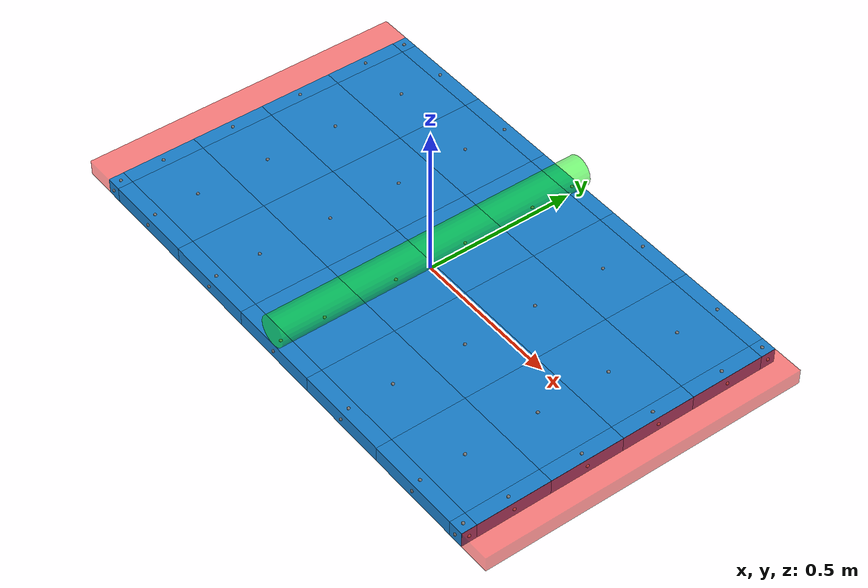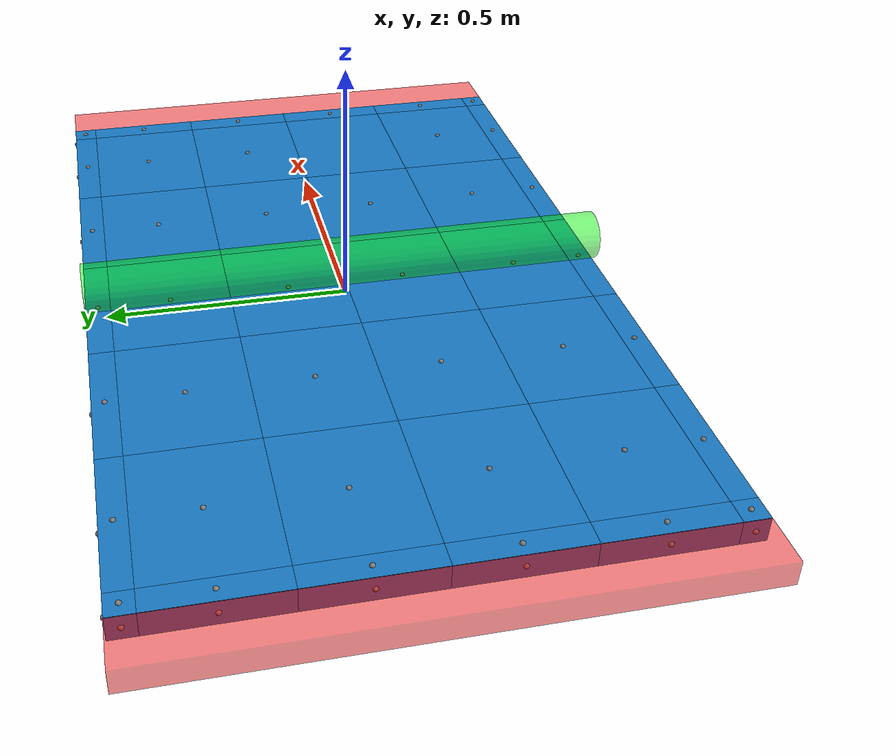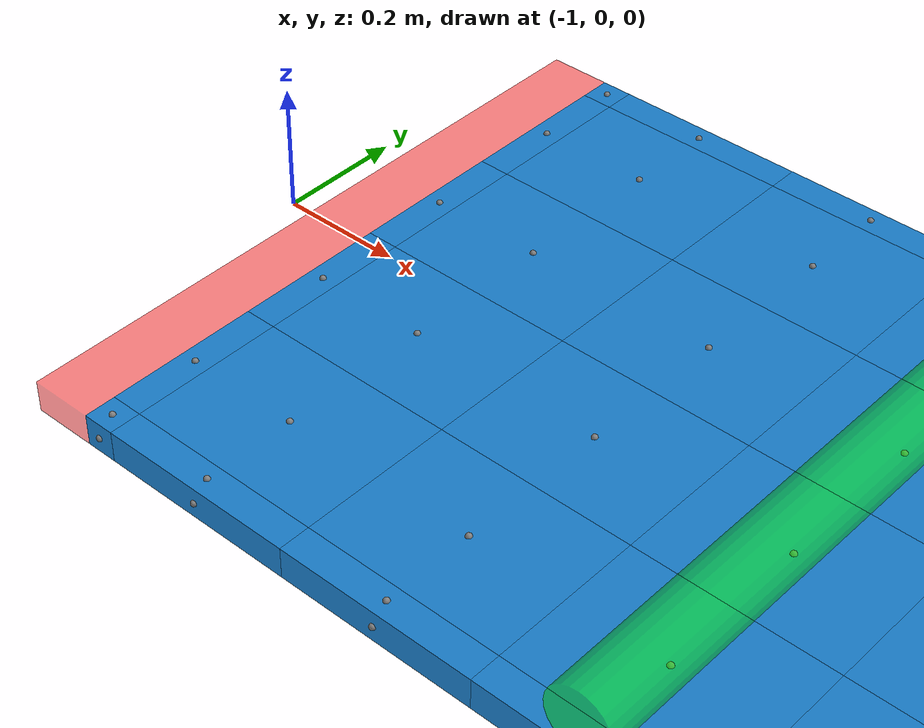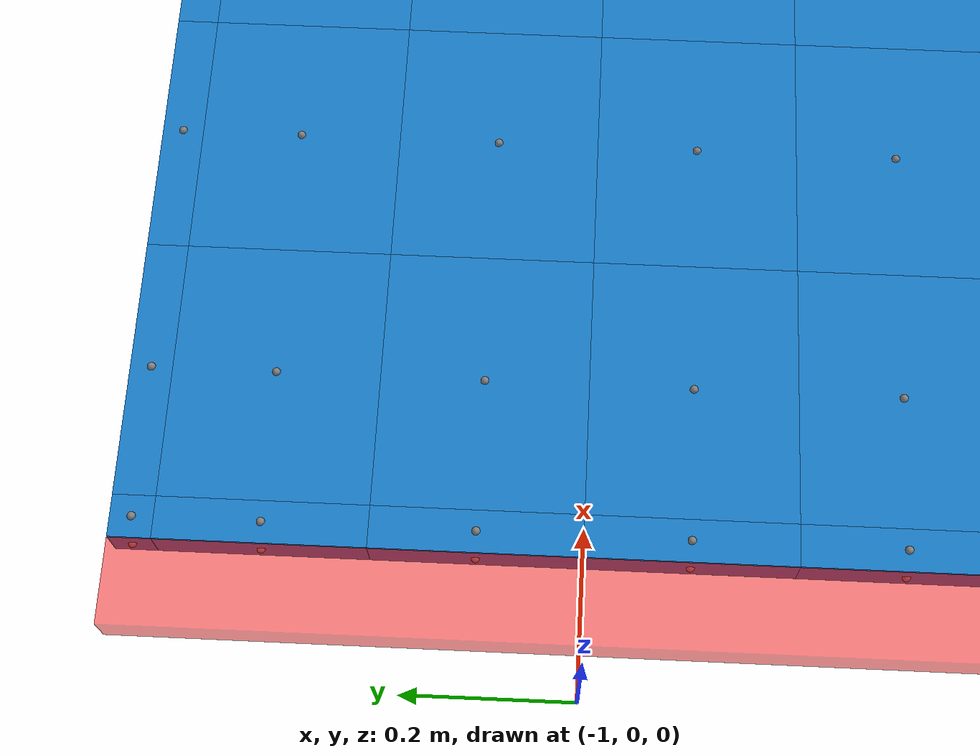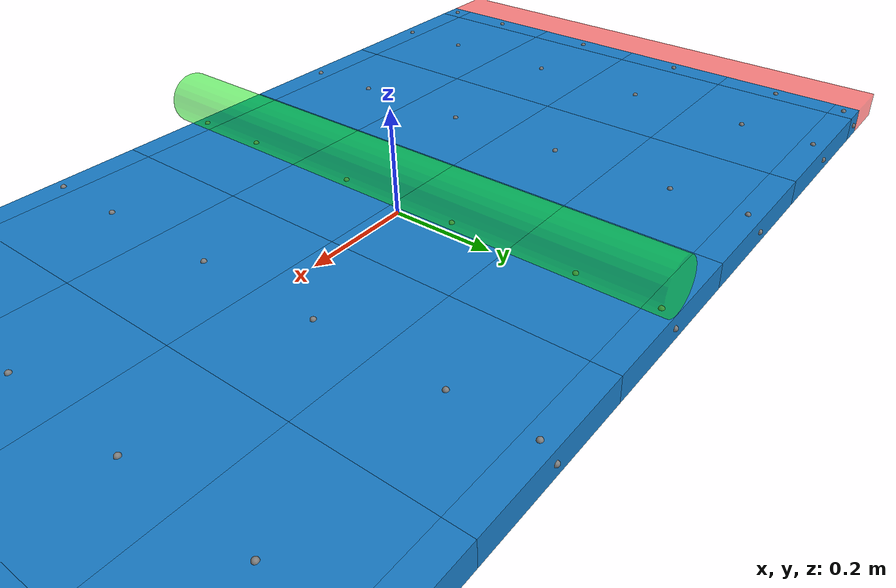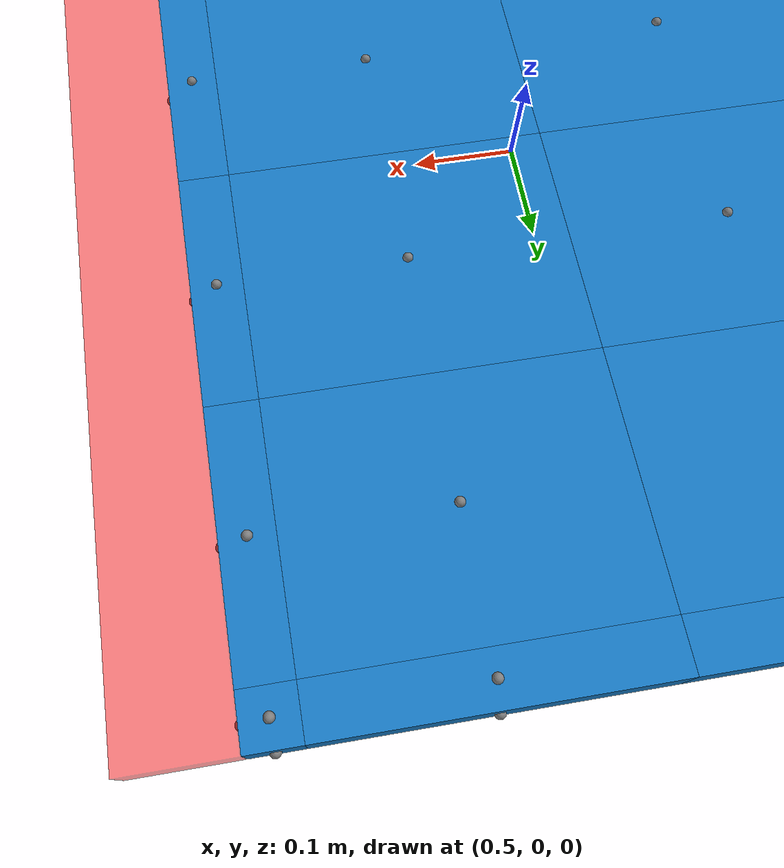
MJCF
<mujoco model="stiffness_test">
  <option integrator="implicitfast" timestep="0.001" gravity="0 0 0"><flag contact="enable"/></option>
  <default>
    <joint armature="0.01" damping="5.0"/>
    <geom friction="0.8" solref="0.02 1.0" solimp="0.9 0.95 0.001"/>
  </default>
  <worldbody>
    <light pos="0 0 5" dir="0 0 -1"/>
    <body name="BChassis">
      <body name="b_bchassis_0_0_0" pos="-0.81500 -0.51500 0.00000">
        <joint type="slide" axis="1 0 0"/>
        <joint type="slide" axis="0 1 0"/>
        <joint type="slide" axis="0 0 1"/>
        <joint type="ball"/>
        <geom type="box" size="0.02500 0.02500 0.02500" mass="0.006889" rgba="0.1 0.5 0.8 1.0" contype="4" conaffinity="2" friction="0.8" solref="0.01 1.0" solimp="0.9 0.95 0.001 0.5 2.0"/>
        <site name="s_BChassis_0_0_0_PX" pos="0.02500 0 0"/>
        <site name="s_BChassis_0_0_0_NX" pos="-0.02500 0 0"/>
        <site name="s_BChassis_0_0_0_PY" pos="0 0.02500 0"/>
        <site name="s_BChassis_0_0_0_NY" pos="0 -0.02500 0"/>
        <site name="s_BChassis_0_0_0_PZ" pos="0 0 0.02500"/>
        <site name="s_BChassis_0_0_0_NZ" pos="0 0 -0.02500"/>
      </body>
      <body name="b_bchassis_0_1_0" pos="-0.81500 -0.36750 0.00000">
        <joint type="slide" axis="1 0 0"/>
        <joint type="slide" axis="0 1 0"/>
        <joint type="slide" axis="0 0 1"/>
        <joint type="ball"/>
        <geom type="box" size="0.02500 0.12250 0.02500" mass="0.033758" rgba="0.1 0.5 0.8 1.0" contype="4" conaffinity="2" friction="0.8" solref="0.01 1.0" solimp="0.9 0.95 0.001 0.5 2.0"/>
        <site name="s_BChassis_0_1_0_PX" pos="0.02500 0 0"/>
        <site name="s_BChassis_0_1_0_NX" pos="-0.02500 0 0"/>
        <site name="s_BChassis_0_1_0_PY" pos="0 0.12250 0"/>
        <site name="s_BChassis_0_1_0_NY" pos="0 -0.12250 0"/>
        <site name="s_BChassis_0_1_0_PZ" pos="0 0 0.02500"/>
        <site name="s_BChassis_0_1_0_NZ" pos="0 0 -0.02500"/>
      </body>
      <body name="b_bchassis_0_2_0" pos="-0.81500 -0.12250 0.00000">
        <joint type="slide" axis="1 0 0"/>
        <joint type="slide" axis="0 1 0"/>
        <joint type="slide" axis="0 0 1"/>
        <joint type="ball"/>
        <geom type="box" size="0.02500 0.12250 0.02500" mass="0.033758" rgba="0.1 0.5 0.8 1.0" contype="4" conaffinity="2" friction="0.8" solref="0.01 1.0" solimp="0.9 0.95 0.001 0.5 2.0"/>
        <site name="s_BChassis_0_2_0_PX" pos="0.02500 0 0"/>
        <site name="s_BChassis_0_2_0_NX" pos="-0.02500 0 0"/>
        <site name="s_BChassis_0_2_0_PY" pos="0 0.12250 0"/>
        <site name="s_BChassis_0_2_0_NY" pos="0 -0.12250 0"/>
        <site name="s_BChassis_0_2_0_PZ" pos="0 0 0.02500"/>
        <site name="s_BChassis_0_2_0_NZ" pos="0 0 -0.02500"/>
      </body>
      <body name="b_bchassis_0_3_0" pos="-0.81500 0.12250 0.00000">
        <joint type="slide" axis="1 0 0"/>
        <joint type="slide" axis="0 1 0"/>
        <joint type="slide" axis="0 0 1"/>
        <joint type="ball"/>
        <geom type="box" size="0.02500 0.12250 0.02500" mass="0.033758" rgba="0.1 0.5 0.8 1.0" contype="4" conaffinity="2" friction="0.8" solref="0.01 1.0" solimp="0.9 0.95 0.001 0.5 2.0"/>
        <site name="s_BChassis_0_3_0_PX" pos="0.02500 0 0"/>
        <site name="s_BChassis_0_3_0_NX" pos="-0.02500 0 0"/>
        <site name="s_BChassis_0_3_0_PY" pos="0 0.12250 0"/>
        <site name="s_BChassis_0_3_0_NY" pos="0 -0.12250 0"/>
        <site name="s_BChassis_0_3_0_PZ" pos="0 0 0.02500"/>
        <site name="s_BChassis_0_3_0_NZ" pos="0 0 -0.02500"/>
      </body>
      <body name="b_bchassis_0_4_0" pos="-0.81500 0.36750 0.00000">
        <joint type="slide" axis="1 0 0"/>
        <joint type="slide" axis="0 1 0"/>
        <joint type="slide" axis="0 0 1"/>
        <joint type="ball"/>
        <geom type="box" size="0.02500 0.12250 0.02500" mass="0.033758" rgba="0.1 0.5 0.8 1.0" contype="4" conaffinity="2" friction="0.8" solref="0.01 1.0" solimp="0.9 0.95 0.001 0.5 2.0"/>
        <site name="s_BChassis_0_4_0_PX" pos="0.02500 0 0"/>
        <site name="s_BChassis_0_4_0_NX" pos="-0.02500 0 0"/>
        <site name="s_BChassis_0_4_0_PY" pos="0 0.12250 0"/>
        <site name="s_BChassis_0_4_0_NY" pos="0 -0.12250 0"/>
        <site name="s_BChassis_0_4_0_PZ" pos="0 0 0.02500"/>
        <site name="s_BChassis_0_4_0_NZ" pos="0 0 -0.02500"/>
      </body>
      <body name="b_bchassis_0_5_0" pos="-0.81500 0.51500 0.00000">
        <joint type="slide" axis="1 0 0"/>
        <joint type="slide" axis="0 1 0"/>
        <joint type="slide" axis="0 0 1"/>
        <joint type="ball"/>
        <geom type="box" size="0.02500 0.02500 0.02500" mass="0.006889" rgba="0.1 0.5 0.8 1.0" contype="4" conaffinity="2" friction="0.8" solref="0.01 1.0" solimp="0.9 0.95 0.001 0.5 2.0"/>
        <site name="s_BChassis_0_5_0_PX" pos="0.02500 0 0"/>
        <site name="s_BChassis_0_5_0_NX" pos="-0.02500 0 0"/>
        <site name="s_BChassis_0_5_0_PY" pos="0 0.02500 0"/>
        <site name="s_BChassis_0_5_0_NY" pos="0 -0.02500 0"/>
        <site name="s_BChassis_0_5_0_PZ" pos="0 0 0.02500"/>
        <site name="s_BChassis_0_5_0_NZ" pos="0 0 -0.02500"/>
      </body>
      <body name="b_bchassis_1_0_0" pos="-0.63200 -0.51500 0.00000">
        <joint type="slide" axis="1 0 0"/>
        <joint type="slide" axis="0 1 0"/>
        <joint type="slide" axis="0 0 1"/>
        <joint type="ball"/>
        <geom type="box" size="0.15800 0.02500 0.02500" mass="0.043541" rgba="0.1 0.5 0.8 1.0" contype="4" conaffinity="2" friction="0.8" solref="0.01 1.0" solimp="0.9 0.95 0.001 0.5 2.0"/>
        <site name="s_BChassis_1_0_0_PX" pos="0.15800 0 0"/>
        <site name="s_BChassis_1_0_0_NX" pos="-0.15800 0 0"/>
        <site name="s_BChassis_1_0_0_PY" pos="0 0.02500 0"/>
        <site name="s_BChassis_1_0_0_NY" pos="0 -0.02500 0"/>
        <site name="s_BChassis_1_0_0_PZ" pos="0 0 0.02500"/>
        <site name="s_BChassis_1_0_0_NZ" pos="0 0 -0.02500"/>
      </body>
      <body name="b_bchassis_1_1_0" pos="-0.63200 -0.36750 0.00000">
        <joint type="slide" axis="1 0 0"/>
        <joint type="slide" axis="0 1 0"/>
        <joint type="slide" axis="0 0 1"/>
        <joint type="ball"/>
        <geom type="box" size="0.15800 0.12250 0.02500" mass="0.213349" rgba="0.1 0.5 0.8 1.0" contype="4" conaffinity="2" friction="0.8" solref="0.01 1.0" solimp="0.9 0.95 0.001 0.5 2.0"/>
        <site name="s_BChassis_1_1_0_PX" pos="0.15800 0 0"/>
        <site name="s_BChassis_1_1_0_NX" pos="-0.15800 0 0"/>
        <site name="s_BChassis_1_1_0_PY" pos="0 0.12250 0"/>
        <site name="s_BChassis_1_1_0_NY" pos="0 -0.12250 0"/>
        <site name="s_BChassis_1_1_0_PZ" pos="0 0 0.02500"/>
        <site name="s_BChassis_1_1_0_NZ" pos="0 0 -0.02500"/>
      </body>
      <body name="b_bchassis_1_2_0" pos="-0.63200 -0.12250 0.00000">
        <joint type="slide" axis="1 0 0"/>
        <joint type="slide" axis="0 1 0"/>
        <joint type="slide" axis="0 0 1"/>
        <joint type="ball"/>
        <geom type="box" size="0.15800 0.12250 0.02500" mass="0.213349" rgba="0.1 0.5 0.8 1.0" contype="4" conaffinity="2" friction="0.8" solref="0.01 1.0" solimp="0.9 0.95 0.001 0.5 2.0"/>
        <site name="s_BChassis_1_2_0_PX" pos="0.15800 0 0"/>
        <site name="s_BChassis_1_2_0_NX" pos="-0.15800 0 0"/>
        <site name="s_BChassis_1_2_0_PY" pos="0 0.12250 0"/>
        <site name="s_BChassis_1_2_0_NY" pos="0 -0.12250 0"/>
        <site name="s_BChassis_1_2_0_PZ" pos="0 0 0.02500"/>
        <site name="s_BChassis_1_2_0_NZ" pos="0 0 -0.02500"/>
      </body>
      <body name="b_bchassis_1_3_0" pos="-0.63200 0.12250 0.00000">
        <joint type="slide" axis="1 0 0"/>
        <joint type="slide" axis="0 1 0"/>
        <joint type="slide" axis="0 0 1"/>
        <joint type="ball"/>
        <geom type="box" size="0.15800 0.12250 0.02500" mass="0.213349" rgba="0.1 0.5 0.8 1.0" contype="4" conaffinity="2" friction="0.8" solref="0.01 1.0" solimp="0.9 0.95 0.001 0.5 2.0"/>
        <site name="s_BChassis_1_3_0_PX" pos="0.15800 0 0"/>
        <site name="s_BChassis_1_3_0_NX" pos="-0.15800 0 0"/>
        <site name="s_BChassis_1_3_0_PY" pos="0 0.12250 0"/>
        <site name="s_BChassis_1_3_0_NY" pos="0 -0.12250 0"/>
        <site name="s_BChassis_1_3_0_PZ" pos="0 0 0.02500"/>
        <site name="s_BChassis_1_3_0_NZ" pos="0 0 -0.02500"/>
      </body>
      <body name="b_bchassis_1_4_0" pos="-0.63200 0.36750 0.00000">
        <joint type="slide" axis="1 0 0"/>
        <joint type="slide" axis="0 1 0"/>
        <joint type="slide" axis="0 0 1"/>
        <joint type="ball"/>
        <geom type="box" size="0.15800 0.12250 0.02500" mass="0.213349" rgba="0.1 0.5 0.8 1.0" contype="4" conaffinity="2" friction="0.8" solref="0.01 1.0" solimp="0.9 0.95 0.001 0.5 2.0"/>
        <site name="s_BChassis_1_4_0_PX" pos="0.15800 0 0"/>
        <site name="s_BChassis_1_4_0_NX" pos="-0.15800 0 0"/>
        <site name="s_BChassis_1_4_0_PY" pos="0 0.12250 0"/>
        <site name="s_BChassis_1_4_0_NY" pos="0 -0.12250 0"/>
        <site name="s_BChassis_1_4_0_PZ" pos="0 0 0.02500"/>
        <site name="s_BChassis_1_4_0_NZ" pos="0 0 -0.02500"/>
      </body>
      <body name="b_bchassis_1_5_0" pos="-0.63200 0.51500 0.00000">
        <joint type="slide" axis="1 0 0"/>
        <joint type="slide" axis="0 1 0"/>
        <joint type="slide" axis="0 0 1"/>
        <joint type="ball"/>
        <geom type="box" size="0.15800 0.02500 0.02500" mass="0.043541" rgba="0.1 0.5 0.8 1.0" contype="4" conaffinity="2" friction="0.8" solref="0.01 1.0" solimp="0.9 0.95 0.001 0.5 2.0"/>
        <site name="s_BChassis_1_5_0_PX" pos="0.15800 0 0"/>
        <site name="s_BChassis_1_5_0_NX" pos="-0.15800 0 0"/>
        <site name="s_BChassis_1_5_0_PY" pos="0 0.02500 0"/>
        <site name="s_BChassis_1_5_0_NY" pos="0 -0.02500 0"/>
        <site name="s_BChassis_1_5_0_PZ" pos="0 0 0.02500"/>
        <site name="s_BChassis_1_5_0_NZ" pos="0 0 -0.02500"/>
      </body>
      <body name="b_bchassis_2_0_0" pos="-0.31600 -0.51500 0.00000">
        <joint type="slide" axis="1 0 0"/>
        <joint type="slide" axis="0 1 0"/>
        <joint type="slide" axis="0 0 1"/>
        <joint type="ball"/>
        <geom type="box" size="0.15800 0.02500 0.02500" mass="0.043541" rgba="0.1 0.5 0.8 1.0" contype="4" conaffinity="2" friction="0.8" solref="0.01 1.0" solimp="0.9 0.95 0.001 0.5 2.0"/>
        <site name="s_BChassis_2_0_0_PX" pos="0.15800 0 0"/>
        <site name="s_BChassis_2_0_0_NX" pos="-0.15800 0 0"/>
        <site name="s_BChassis_2_0_0_PY" pos="0 0.02500 0"/>
        <site name="s_BChassis_2_0_0_NY" pos="0 -0.02500 0"/>
        <site name="s_BChassis_2_0_0_PZ" pos="0 0 0.02500"/>
        <site name="s_BChassis_2_0_0_NZ" pos="0 0 -0.02500"/>
      </body>
      <body name="b_bchassis_2_1_0" pos="-0.31600 -0.36750 0.00000">
        <joint type="slide" axis="1 0 0"/>
        <joint type="slide" axis="0 1 0"/>
        <joint type="slide" axis="0 0 1"/>
        <joint type="ball"/>
        <geom type="box" size="0.15800 0.12250 0.02500" mass="0.213349" rgba="0.1 0.5 0.8 1.0" contype="4" conaffinity="2" friction="0.8" solref="0.01 1.0" solimp="0.9 0.95 0.001 0.5 2.0"/>
        <site name="s_BChassis_2_1_0_PX" pos="0.15800 0 0"/>
        <site name="s_BChassis_2_1_0_NX" pos="-0.15800 0 0"/>
        <site name="s_BChassis_2_1_0_PY" pos="0 0.12250 0"/>
        <site name="s_BChassis_2_1_0_NY" pos="0 -0.12250 0"/>
        <site name="s_BChassis_2_1_0_PZ" pos="0 0 0.02500"/>
        <site name="s_BChassis_2_1_0_NZ" pos="0 0 -0.02500"/>
      </body>
      <body name="b_bchassis_2_2_0" pos="-0.31600 -0.12250 0.00000">
        <joint type="slide" axis="1 0 0"/>
        <joint type="slide" axis="0 1 0"/>
        <joint type="slide" axis="0 0 1"/>
        <joint type="ball"/>
        <geom type="box" size="0.15800 0.12250 0.02500" mass="0.213349" rgba="0.1 0.5 0.8 1.0" contype="4" conaffinity="2" friction="0.8" solref="0.01 1.0" solimp="0.9 0.95 0.001 0.5 2.0"/>
        <site name="s_BChassis_2_2_0_PX" pos="0.15800 0 0"/>
        <site name="s_BChassis_2_2_0_NX" pos="-0.15800 0 0"/>
        <site name="s_BChassis_2_2_0_PY" pos="0 0.12250 0"/>
        <site name="s_BChassis_2_2_0_NY" pos="0 -0.12250 0"/>
        <site name="s_BChassis_2_2_0_PZ" pos="0 0 0.02500"/>
        <site name="s_BChassis_2_2_0_NZ" pos="0 0 -0.02500"/>
      </body>
      <body name="b_bchassis_2_3_0" pos="-0.31600 0.12250 0.00000">
        <joint type="slide" axis="1 0 0"/>
        <joint type="slide" axis="0 1 0"/>
        <joint type="slide" axis="0 0 1"/>
        <joint type="ball"/>
        <geom type="box" size="0.15800 0.12250 0.02500" mass="0.213349" rgba="0.1 0.5 0.8 1.0" contype="4" conaffinity="2" friction="0.8" solref="0.01 1.0" solimp="0.9 0.95 0.001 0.5 2.0"/>
        <site name="s_BChassis_2_3_0_PX" pos="0.15800 0 0"/>
        <site name="s_BChassis_2_3_0_NX" pos="-0.15800 0 0"/>
        <site name="s_BChassis_2_3_0_PY" pos="0 0.12250 0"/>
        <site name="s_BChassis_2_3_0_NY" pos="0 -0.12250 0"/>
        <site name="s_BChassis_2_3_0_PZ" pos="0 0 0.02500"/>
        <site name="s_BChassis_2_3_0_NZ" pos="0 0 -0.02500"/>
      </body>
      <body name="b_bchassis_2_4_0" pos="-0.31600 0.36750 0.00000">
        <joint type="slide" axis="1 0 0"/>
        <joint type="slide" axis="0 1 0"/>
        <joint type="slide" axis="0 0 1"/>
        <joint type="ball"/>
        <geom type="box" size="0.15800 0.12250 0.02500" mass="0.213349" rgba="0.1 0.5 0.8 1.0" contype="4" conaffinity="2" friction="0.8" solref="0.01 1.0" solimp="0.9 0.95 0.001 0.5 2.0"/>
        <site name="s_BChassis_2_4_0_PX" pos="0.15800 0 0"/>
        <site name="s_BChassis_2_4_0_NX" pos="-0.15800 0 0"/>
        <site name="s_BChassis_2_4_0_PY" pos="0 0.12250 0"/>
        <site name="s_BChassis_2_4_0_NY" pos="0 -0.12250 0"/>
        <site name="s_BChassis_2_4_0_PZ" pos="0 0 0.02500"/>
        <site name="s_BChassis_2_4_0_NZ" pos="0 0 -0.02500"/>
      </body>
      <body name="b_bchassis_2_5_0" pos="-0.31600 0.51500 0.00000">
        <joint type="slide" axis="1 0 0"/>
        <joint type="slide" axis="0 1 0"/>
        <joint type="slide" axis="0 0 1"/>
        <joint type="ball"/>
        <geom type="box" size="0.15800 0.02500 0.02500" mass="0.043541" rgba="0.1 0.5 0.8 1.0" contype="4" conaffinity="2" friction="0.8" solref="0.01 1.0" solimp="0.9 0.95 0.001 0.5 2.0"/>
        <site name="s_BChassis_2_5_0_PX" pos="0.15800 0 0"/>
        <site name="s_BChassis_2_5_0_NX" pos="-0.15800 0 0"/>
        <site name="s_BChassis_2_5_0_PY" pos="0 0.02500 0"/>
        <site name="s_BChassis_2_5_0_NY" pos="0 -0.02500 0"/>
        <site name="s_BChassis_2_5_0_PZ" pos="0 0 0.02500"/>
        <site name="s_BChassis_2_5_0_NZ" pos="0 0 -0.02500"/>
      </body>
      <body name="b_bchassis_3_0_0" pos="0.00000 -0.51500 0.00000">
        <joint type="slide" axis="1 0 0"/>
        <joint type="slide" axis="0 1 0"/>
        <joint type="slide" axis="0 0 1"/>
        <joint type="ball"/>
        <geom type="box" size="0.15800 0.02500 0.02500" mass="0.043541" rgba="0.1 0.5 0.8 1.0" contype="4" conaffinity="2" friction="0.8" solref="0.01 1.0" solimp="0.9 0.95 0.001 0.5 2.0"/>
        <site name="s_BChassis_3_0_0_PX" pos="0.15800 0 0"/>
        <site name="s_BChassis_3_0_0_NX" pos="-0.15800 0 0"/>
        <site name="s_BChassis_3_0_0_PY" pos="0 0.02500 0"/>
        <site name="s_BChassis_3_0_0_NY" pos="0 -0.02500 0"/>
        <site name="s_BChassis_3_0_0_PZ" pos="0 0 0.02500"/>
        <site name="s_BChassis_3_0_0_NZ" pos="0 0 -0.02500"/>
      </body>
      <body name="b_bchassis_3_1_0" pos="0.00000 -0.36750 0.00000">
        <joint type="slide" axis="1 0 0"/>
        <joint type="slide" axis="0 1 0"/>
        <joint type="slide" axis="0 0 1"/>
        <joint type="ball"/>
        <geom type="box" size="0.15800 0.12250 0.02500" mass="0.213349" rgba="0.1 0.5 0.8 1.0" contype="4" conaffinity="2" friction="0.8" solref="0.01 1.0" solimp="0.9 0.95 0.001 0.5 2.0"/>
        <site name="s_BChassis_3_1_0_PX" pos="0.15800 0 0"/>
        <site name="s_BChassis_3_1_0_NX" pos="-0.15800 0 0"/>
        <site name="s_BChassis_3_1_0_PY" pos="0 0.12250 0"/>
        <site name="s_BChassis_3_1_0_NY" pos="0 -0.12250 0"/>
        <site name="s_BChassis_3_1_0_PZ" pos="0 0 0.02500"/>
        <site name="s_BChassis_3_1_0_NZ" pos="0 0 -0.02500"/>
      </body>
      <body name="b_bchassis_3_2_0" pos="0.00000 -0.12250 0.00000">
        <joint type="slide" axis="1 0 0"/>
        <joint type="slide" axis="0 1 0"/>
        <joint type="slide" axis="0 0 1"/>
        <joint type="ball"/>
        <geom type="box" size="0.15800 0.12250 0.02500" mass="0.213349" rgba="0.1 0.5 0.8 1.0" contype="4" conaffinity="2" friction="0.8" solref="0.01 1.0" solimp="0.9 0.95 0.001 0.5 2.0"/>
        <site name="s_BChassis_3_2_0_PX" pos="0.15800 0 0"/>
        <site name="s_BChassis_3_2_0_NX" pos="-0.15800 0 0"/>
        <site name="s_BChassis_3_2_0_PY" pos="0 0.12250 0"/>
        <site name="s_BChassis_3_2_0_NY" pos="0 -0.12250 0"/>
        <site name="s_BChassis_3_2_0_PZ" pos="0 0 0.02500"/>
        <site name="s_BChassis_3_2_0_NZ" pos="0 0 -0.02500"/>
      </body>
      <body name="b_bchassis_3_3_0" pos="0.00000 0.12250 0.00000">
        <joint type="slide" axis="1 0 0"/>
        <joint type="slide" axis="0 1 0"/>
        <joint type="slide" axis="0 0 1"/>
        <joint type="ball"/>
        <geom type="box" size="0.15800 0.12250 0.02500" mass="0.213349" rgba="0.1 0.5 0.8 1.0" contype="4" conaffinity="2" friction="0.8" solref="0.01 1.0" solimp="0.9 0.95 0.001 0.5 2.0"/>
        <site name="s_BChassis_3_3_0_PX" pos="0.15800 0 0"/>
        <site name="s_BChassis_3_3_0_NX" pos="-0.15800 0 0"/>
        <site name="s_BChassis_3_3_0_PY" pos="0 0.12250 0"/>
        <site name="s_BChassis_3_3_0_NY" pos="0 -0.12250 0"/>
        <site name="s_BChassis_3_3_0_PZ" pos="0 0 0.02500"/>
        <site name="s_BChassis_3_3_0_NZ" pos="0 0 -0.02500"/>
      </body>
      <body name="b_bchassis_3_4_0" pos="0.00000 0.36750 0.00000">
        <joint type="slide" axis="1 0 0"/>
        <joint type="slide" axis="0 1 0"/>
        <joint type="slide" axis="0 0 1"/>
        <joint type="ball"/>
        <geom type="box" size="0.15800 0.12250 0.02500" mass="0.213349" rgba="0.1 0.5 0.8 1.0" contype="4" conaffinity="2" friction="0.8" solref="0.01 1.0" solimp="0.9 0.95 0.001 0.5 2.0"/>
        <site name="s_BChassis_3_4_0_PX" pos="0.15800 0 0"/>
        <site name="s_BChassis_3_4_0_NX" pos="-0.15800 0 0"/>
        <site name="s_BChassis_3_4_0_PY" pos="0 0.12250 0"/>
        <site name="s_BChassis_3_4_0_NY" pos="0 -0.12250 0"/>
        <site name="s_BChassis_3_4_0_PZ" pos="0 0 0.02500"/>
        <site name="s_BChassis_3_4_0_NZ" pos="0 0 -0.02500"/>
      </body>
      <body name="b_bchassis_3_5_0" pos="0.00000 0.51500 0.00000">
        <joint type="slide" axis="1 0 0"/>
        <joint type="slide" axis="0 1 0"/>
        <joint type="slide" axis="0 0 1"/>
        <joint type="ball"/>
        <geom type="box" size="0.15800 0.02500 0.02500" mass="0.043541" rgba="0.1 0.5 0.8 1.0" contype="4" conaffinity="2" friction="0.8" solref="0.01 1.0" solimp="0.9 0.95 0.001 0.5 2.0"/>
        <site name="s_BChassis_3_5_0_PX" pos="0.15800 0 0"/>
        <site name="s_BChassis_3_5_0_NX" pos="-0.15800 0 0"/>
        <site name="s_BChassis_3_5_0_PY" pos="0 0.02500 0"/>
        <site name="s_BChassis_3_5_0_NY" pos="0 -0.02500 0"/>
        <site name="s_BChassis_3_5_0_PZ" pos="0 0 0.02500"/>
        <site name="s_BChassis_3_5_0_NZ" pos="0 0 -0.02500"/>
      </body>
      <body name="b_bchassis_4_0_0" pos="0.31600 -0.51500 0.00000">
        <joint type="slide" axis="1 0 0"/>
        <joint type="slide" axis="0 1 0"/>
        <joint type="slide" axis="0 0 1"/>
        <joint type="ball"/>
        <geom type="box" size="0.15800 0.02500 0.02500" mass="0.043541" rgba="0.1 0.5 0.8 1.0" contype="4" conaffinity="2" friction="0.8" solref="0.01 1.0" solimp="0.9 0.95 0.001 0.5 2.0"/>
        <site name="s_BChassis_4_0_0_PX" pos="0.15800 0 0"/>
        <site name="s_BChassis_4_0_0_NX" pos="-0.15800 0 0"/>
        <site name="s_BChassis_4_0_0_PY" pos="0 0.02500 0"/>
        <site name="s_BChassis_4_0_0_NY" pos="0 -0.02500 0"/>
        <site name="s_BChassis_4_0_0_PZ" pos="0 0 0.02500"/>
        <site name="s_BChassis_4_0_0_NZ" pos="0 0 -0.02500"/>
      </body>
      <body name="b_bchassis_4_1_0" pos="0.31600 -0.36750 0.00000">
        <joint type="slide" axis="1 0 0"/>
        <joint type="slide" axis="0 1 0"/>
        <joint type="slide" axis="0 0 1"/>
        <joint type="ball"/>
        <geom type="box" size="0.15800 0.12250 0.02500" mass="0.213349" rgba="0.1 0.5 0.8 1.0" contype="4" conaffinity="2" friction="0.8" solref="0.01 1.0" solimp="0.9 0.95 0.001 0.5 2.0"/>
        <site name="s_BChassis_4_1_0_PX" pos="0.15800 0 0"/>
        <site name="s_BChassis_4_1_0_NX" pos="-0.15800 0 0"/>
        <site name="s_BChassis_4_1_0_PY" pos="0 0.12250 0"/>
        <site name="s_BChassis_4_1_0_NY" pos="0 -0.12250 0"/>
        <site name="s_BChassis_4_1_0_PZ" pos="0 0 0.02500"/>
        <site name="s_BChassis_4_1_0_NZ" pos="0 0 -0.02500"/>
      </body>
      <body name="b_bchassis_4_2_0" pos="0.31600 -0.12250 0.00000">
        <joint type="slide" axis="1 0 0"/>
        <joint type="slide" axis="0 1 0"/>
        <joint type="slide" axis="0 0 1"/>
        <joint type="ball"/>
        <geom type="box" size="0.15800 0.12250 0.02500" mass="0.213349" rgba="0.1 0.5 0.8 1.0" contype="4" conaffinity="2" friction="0.8" solref="0.01 1.0" solimp="0.9 0.95 0.001 0.5 2.0"/>
        <site name="s_BChassis_4_2_0_PX" pos="0.15800 0 0"/>
        <site name="s_BChassis_4_2_0_NX" pos="-0.15800 0 0"/>
        <site name="s_BChassis_4_2_0_PY" pos="0 0.12250 0"/>
        <site name="s_BChassis_4_2_0_NY" pos="0 -0.12250 0"/>
        <site name="s_BChassis_4_2_0_PZ" pos="0 0 0.02500"/>
        <site name="s_BChassis_4_2_0_NZ" pos="0 0 -0.02500"/>
      </body>
      <body name="b_bchassis_4_3_0" pos="0.31600 0.12250 0.00000">
        <joint type="slide" axis="1 0 0"/>
        <joint type="slide" axis="0 1 0"/>
        <joint type="slide" axis="0 0 1"/>
        <joint type="ball"/>
        <geom type="box" size="0.15800 0.12250 0.02500" mass="0.213349" rgba="0.1 0.5 0.8 1.0" contype="4" conaffinity="2" friction="0.8" solref="0.01 1.0" solimp="0.9 0.95 0.001 0.5 2.0"/>
        <site name="s_BChassis_4_3_0_PX" pos="0.15800 0 0"/>
        <site name="s_BChassis_4_3_0_NX" pos="-0.15800 0 0"/>
        <site name="s_BChassis_4_3_0_PY" pos="0 0.12250 0"/>
        <site name="s_BChassis_4_3_0_NY" pos="0 -0.12250 0"/>
        <site name="s_BChassis_4_3_0_PZ" pos="0 0 0.02500"/>
        <site name="s_BChassis_4_3_0_NZ" pos="0 0 -0.02500"/>
      </body>
      <body name="b_bchassis_4_4_0" pos="0.31600 0.36750 0.00000">
        <joint type="slide" axis="1 0 0"/>
        <joint type="slide" axis="0 1 0"/>
        <joint type="slide" axis="0 0 1"/>
        <joint type="ball"/>
        <geom type="box" size="0.15800 0.12250 0.02500" mass="0.213349" rgba="0.1 0.5 0.8 1.0" contype="4" conaffinity="2" friction="0.8" solref="0.01 1.0" solimp="0.9 0.95 0.001 0.5 2.0"/>
        <site name="s_BChassis_4_4_0_PX" pos="0.15800 0 0"/>
        <site name="s_BChassis_4_4_0_NX" pos="-0.15800 0 0"/>
        <site name="s_BChassis_4_4_0_PY" pos="0 0.12250 0"/>
        <site name="s_BChassis_4_4_0_NY" pos="0 -0.12250 0"/>
        <site name="s_BChassis_4_4_0_PZ" pos="0 0 0.02500"/>
        <site name="s_BChassis_4_4_0_NZ" pos="0 0 -0.02500"/>
      </body>
      <body name="b_bchassis_4_5_0" pos="0.31600 0.51500 0.00000">
        <joint type="slide" axis="1 0 0"/>
        <joint type="slide" axis="0 1 0"/>
        <joint type="slide" axis="0 0 1"/>
        <joint type="ball"/>
        <geom type="box" size="0.15800 0.02500 0.02500" mass="0.043541" rgba="0.1 0.5 0.8 1.0" contype="4" conaffinity="2" friction="0.8" solref="0.01 1.0" solimp="0.9 0.95 0.001 0.5 2.0"/>
        <site name="s_BChassis_4_5_0_PX" pos="0.15800 0 0"/>
        <site name="s_BChassis_4_5_0_NX" pos="-0.15800 0 0"/>
        <site name="s_BChassis_4_5_0_PY" pos="0 0.02500 0"/>
        <site name="s_BChassis_4_5_0_NY" pos="0 -0.02500 0"/>
        <site name="s_BChassis_4_5_0_PZ" pos="0 0 0.02500"/>
        <site name="s_BChassis_4_5_0_NZ" pos="0 0 -0.02500"/>
      </body>
      <body name="b_bchassis_5_0_0" pos="0.63200 -0.51500 0.00000">
        <joint type="slide" axis="1 0 0"/>
        <joint type="slide" axis="0 1 0"/>
        <joint type="slide" axis="0 0 1"/>
        <joint type="ball"/>
        <geom type="box" size="0.15800 0.02500 0.02500" mass="0.043541" rgba="0.1 0.5 0.8 1.0" contype="4" conaffinity="2" friction="0.8" solref="0.01 1.0" solimp="0.9 0.95 0.001 0.5 2.0"/>
        <site name="s_BChassis_5_0_0_PX" pos="0.15800 0 0"/>
        <site name="s_BChassis_5_0_0_NX" pos="-0.15800 0 0"/>
        <site name="s_BChassis_5_0_0_PY" pos="0 0.02500 0"/>
        <site name="s_BChassis_5_0_0_NY" pos="0 -0.02500 0"/>
        <site name="s_BChassis_5_0_0_PZ" pos="0 0 0.02500"/>
        <site name="s_BChassis_5_0_0_NZ" pos="0 0 -0.02500"/>
      </body>
      <body name="b_bchassis_5_1_0" pos="0.63200 -0.36750 0.00000">
        <joint type="slide" axis="1 0 0"/>
        <joint type="slide" axis="0 1 0"/>
        <joint type="slide" axis="0 0 1"/>
        <joint type="ball"/>
        <geom type="box" size="0.15800 0.12250 0.02500" mass="0.213349" rgba="0.1 0.5 0.8 1.0" contype="4" conaffinity="2" friction="0.8" solref="0.01 1.0" solimp="0.9 0.95 0.001 0.5 2.0"/>
        <site name="s_BChassis_5_1_0_PX" pos="0.15800 0 0"/>
        <site name="s_BChassis_5_1_0_NX" pos="-0.15800 0 0"/>
        <site name="s_BChassis_5_1_0_PY" pos="0 0.12250 0"/>
        <site name="s_BChassis_5_1_0_NY" pos="0 -0.12250 0"/>
        <site name="s_BChassis_5_1_0_PZ" pos="0 0 0.02500"/>
        <site name="s_BChassis_5_1_0_NZ" pos="0 0 -0.02500"/>
      </body>
      <body name="b_bchassis_5_2_0" pos="0.63200 -0.12250 0.00000">
        <joint type="slide" axis="1 0 0"/>
        <joint type="slide" axis="0 1 0"/>
        <joint type="slide" axis="0 0 1"/>
        <joint type="ball"/>
        <geom type="box" size="0.15800 0.12250 0.02500" mass="0.213349" rgba="0.1 0.5 0.8 1.0" contype="4" conaffinity="2" friction="0.8" solref="0.01 1.0" solimp="0.9 0.95 0.001 0.5 2.0"/>
        <site name="s_BChassis_5_2_0_PX" pos="0.15800 0 0"/>
        <site name="s_BChassis_5_2_0_NX" pos="-0.15800 0 0"/>
        <site name="s_BChassis_5_2_0_PY" pos="0 0.12250 0"/>
        <site name="s_BChassis_5_2_0_NY" pos="0 -0.12250 0"/>
        <site name="s_BChassis_5_2_0_PZ" pos="0 0 0.02500"/>
        <site name="s_BChassis_5_2_0_NZ" pos="0 0 -0.02500"/>
      </body>
      <body name="b_bchassis_5_3_0" pos="0.63200 0.12250 0.00000">
        <joint type="slide" axis="1 0 0"/>
        <joint type="slide" axis="0 1 0"/>
        <joint type="slide" axis="0 0 1"/>
        <joint type="ball"/>
        <geom type="box" size="0.15800 0.12250 0.02500" mass="0.213349" rgba="0.1 0.5 0.8 1.0" contype="4" conaffinity="2" friction="0.8" solref="0.01 1.0" solimp="0.9 0.95 0.001 0.5 2.0"/>
        <site name="s_BChassis_5_3_0_PX" pos="0.15800 0 0"/>
        <site name="s_BChassis_5_3_0_NX" pos="-0.15800 0 0"/>
        <site name="s_BChassis_5_3_0_PY" pos="0 0.12250 0"/>
        <site name="s_BChassis_5_3_0_NY" pos="0 -0.12250 0"/>
        <site name="s_BChassis_5_3_0_PZ" pos="0 0 0.02500"/>
        <site name="s_BChassis_5_3_0_NZ" pos="0 0 -0.02500"/>
      </body>
      <body name="b_bchassis_5_4_0" pos="0.63200 0.36750 0.00000">
        <joint type="slide" axis="1 0 0"/>
        <joint type="slide" axis="0 1 0"/>
        <joint type="slide" axis="0 0 1"/>
        <joint type="ball"/>
        <geom type="box" size="0.15800 0.12250 0.02500" mass="0.213349" rgba="0.1 0.5 0.8 1.0" contype="4" conaffinity="2" friction="0.8" solref="0.01 1.0" solimp="0.9 0.95 0.001 0.5 2.0"/>
        <site name="s_BChassis_5_4_0_PX" pos="0.15800 0 0"/>
        <site name="s_BChassis_5_4_0_NX" pos="-0.15800 0 0"/>
        <site name="s_BChassis_5_4_0_PY" pos="0 0.12250 0"/>
        <site name="s_BChassis_5_4_0_NY" pos="0 -0.12250 0"/>
        <site name="s_BChassis_5_4_0_PZ" pos="0 0 0.02500"/>
        <site name="s_BChassis_5_4_0_NZ" pos="0 0 -0.02500"/>
      </body>
      <body name="b_bchassis_5_5_0" pos="0.63200 0.51500 0.00000">
        <joint type="slide" axis="1 0 0"/>
        <joint type="slide" axis="0 1 0"/>
        <joint type="slide" axis="0 0 1"/>
        <joint type="ball"/>
        <geom type="box" size="0.15800 0.02500 0.02500" mass="0.043541" rgba="0.1 0.5 0.8 1.0" contype="4" conaffinity="2" friction="0.8" solref="0.01 1.0" solimp="0.9 0.95 0.001 0.5 2.0"/>
        <site name="s_BChassis_5_5_0_PX" pos="0.15800 0 0"/>
        <site name="s_BChassis_5_5_0_NX" pos="-0.15800 0 0"/>
        <site name="s_BChassis_5_5_0_PY" pos="0 0.02500 0"/>
        <site name="s_BChassis_5_5_0_NY" pos="0 -0.02500 0"/>
        <site name="s_BChassis_5_5_0_PZ" pos="0 0 0.02500"/>
        <site name="s_BChassis_5_5_0_NZ" pos="0 0 -0.02500"/>
      </body>
      <body name="b_bchassis_6_0_0" pos="0.81500 -0.51500 0.00000">
        <joint type="slide" axis="1 0 0"/>
        <joint type="slide" axis="0 1 0"/>
        <joint type="slide" axis="0 0 1"/>
        <joint type="ball"/>
        <geom type="box" size="0.02500 0.02500 0.02500" mass="0.006889" rgba="0.1 0.5 0.8 1.0" contype="4" conaffinity="2" friction="0.8" solref="0.01 1.0" solimp="0.9 0.95 0.001 0.5 2.0"/>
        <site name="s_BChassis_6_0_0_PX" pos="0.02500 0 0"/>
        <site name="s_BChassis_6_0_0_NX" pos="-0.02500 0 0"/>
        <site name="s_BChassis_6_0_0_PY" pos="0 0.02500 0"/>
        <site name="s_BChassis_6_0_0_NY" pos="0 -0.02500 0"/>
        <site name="s_BChassis_6_0_0_PZ" pos="0 0 0.02500"/>
        <site name="s_BChassis_6_0_0_NZ" pos="0 0 -0.02500"/>
      </body>
      <body name="b_bchassis_6_1_0" pos="0.81500 -0.36750 0.00000">
        <joint type="slide" axis="1 0 0"/>
        <joint type="slide" axis="0 1 0"/>
        <joint type="slide" axis="0 0 1"/>
        <joint type="ball"/>
        <geom type="box" size="0.02500 0.12250 0.02500" mass="0.033758" rgba="0.1 0.5 0.8 1.0" contype="4" conaffinity="2" friction="0.8" solref="0.01 1.0" solimp="0.9 0.95 0.001 0.5 2.0"/>
        <site name="s_BChassis_6_1_0_PX" pos="0.02500 0 0"/>
        <site name="s_BChassis_6_1_0_NX" pos="-0.02500 0 0"/>
        <site name="s_BChassis_6_1_0_PY" pos="0 0.12250 0"/>
        <site name="s_BChassis_6_1_0_NY" pos="0 -0.12250 0"/>
        <site name="s_BChassis_6_1_0_PZ" pos="0 0 0.02500"/>
        <site name="s_BChassis_6_1_0_NZ" pos="0 0 -0.02500"/>
      </body>
      <body name="b_bchassis_6_2_0" pos="0.81500 -0.12250 0.00000">
        <joint type="slide" axis="1 0 0"/>
        <joint type="slide" axis="0 1 0"/>
        <joint type="slide" axis="0 0 1"/>
        <joint type="ball"/>
        <geom type="box" size="0.02500 0.12250 0.02500" mass="0.033758" rgba="0.1 0.5 0.8 1.0" contype="4" conaffinity="2" friction="0.8" solref="0.01 1.0" solimp="0.9 0.95 0.001 0.5 2.0"/>
        <site name="s_BChassis_6_2_0_PX" pos="0.02500 0 0"/>
        <site name="s_BChassis_6_2_0_NX" pos="-0.02500 0 0"/>
        <site name="s_BChassis_6_2_0_PY" pos="0 0.12250 0"/>
        <site name="s_BChassis_6_2_0_NY" pos="0 -0.12250 0"/>
        <site name="s_BChassis_6_2_0_PZ" pos="0 0 0.02500"/>
        <site name="s_BChassis_6_2_0_NZ" pos="0 0 -0.02500"/>
      </body>
      <body name="b_bchassis_6_3_0" pos="0.81500 0.12250 0.00000">
        <joint type="slide" axis="1 0 0"/>
        <joint type="slide" axis="0 1 0"/>
        <joint type="slide" axis="0 0 1"/>
        <joint type="ball"/>
        <geom type="box" size="0.02500 0.12250 0.02500" mass="0.033758" rgba="0.1 0.5 0.8 1.0" contype="4" conaffinity="2" friction="0.8" solref="0.01 1.0" solimp="0.9 0.95 0.001 0.5 2.0"/>
        <site name="s_BChassis_6_3_0_PX" pos="0.02500 0 0"/>
        <site name="s_BChassis_6_3_0_NX" pos="-0.02500 0 0"/>
        <site name="s_BChassis_6_3_0_PY" pos="0 0.12250 0"/>
        <site name="s_BChassis_6_3_0_NY" pos="0 -0.12250 0"/>
        <site name="s_BChassis_6_3_0_PZ" pos="0 0 0.02500"/>
        <site name="s_BChassis_6_3_0_NZ" pos="0 0 -0.02500"/>
      </body>
      <body name="b_bchassis_6_4_0" pos="0.81500 0.36750 0.00000">
        <joint type="slide" axis="1 0 0"/>
        <joint type="slide" axis="0 1 0"/>
        <joint type="slide" axis="0 0 1"/>
        <joint type="ball"/>
        <geom type="box" size="0.02500 0.12250 0.02500" mass="0.033758" rgba="0.1 0.5 0.8 1.0" contype="4" conaffinity="2" friction="0.8" solref="0.01 1.0" solimp="0.9 0.95 0.001 0.5 2.0"/>
        <site name="s_BChassis_6_4_0_PX" pos="0.02500 0 0"/>
        <site name="s_BChassis_6_4_0_NX" pos="-0.02500 0 0"/>
        <site name="s_BChassis_6_4_0_PY" pos="0 0.12250 0"/>
        <site name="s_BChassis_6_4_0_NY" pos="0 -0.12250 0"/>
        <site name="s_BChassis_6_4_0_PZ" pos="0 0 0.02500"/>
        <site name="s_BChassis_6_4_0_NZ" pos="0 0 -0.02500"/>
      </body>
      <body name="b_bchassis_6_5_0" pos="0.81500 0.51500 0.00000">
        <joint type="slide" axis="1 0 0"/>
        <joint type="slide" axis="0 1 0"/>
        <joint type="slide" axis="0 0 1"/>
        <joint type="ball"/>
        <geom type="box" size="0.02500 0.02500 0.02500" mass="0.006889" rgba="0.1 0.5 0.8 1.0" contype="4" conaffinity="2" friction="0.8" solref="0.01 1.0" solimp="0.9 0.95 0.001 0.5 2.0"/>
        <site name="s_BChassis_6_5_0_PX" pos="0.02500 0 0"/>
        <site name="s_BChassis_6_5_0_NX" pos="-0.02500 0 0"/>
        <site name="s_BChassis_6_5_0_PY" pos="0 0.02500 0"/>
        <site name="s_BChassis_6_5_0_NY" pos="0 -0.02500 0"/>
        <site name="s_BChassis_6_5_0_PZ" pos="0 0 0.02500"/>
        <site name="s_BChassis_6_5_0_NZ" pos="0 0 -0.02500"/>
      </body>
    </body>
    <body name="clamp_L" pos="-0.8909999999999999 0.0 0.0"><geom type="box" size="0.05 0.5399999999999999 0.025" rgba="1 0 0 0.5" contype="0" conaffinity="0"/></body>
    <body name="clamp_R" pos="0.8909999999999999 0.0 0.0"><geom type="box" size="0.05 0.5399999999999999 0.025" rgba="1 0 0 0.5" contype="0" conaffinity="0"/></body>
    <body name="ram" pos="0 0.0 0.076">
      <joint name="ram_z" type="slide" axis="0 0 1"/>
      <geom type="cylinder" size="0.05 0.5399999999999999" euler="90 0 0" rgba="0 1 0 0.5" contype="0" conaffinity="0"/>
    </body>
  </worldbody>
  <actuator>
    <position name="act_ram" joint="ram_z" kp="200000000" kv="100000"/>
  </actuator>
  <equality>
        <weld site1="s_BChassis_0_0_0_PX" site2="s_BChassis_1_0_0_NX" solref="0.01 1.0" solimp="0.9 0.95 0.001 0.5 2.0"/>
        <weld site1="s_BChassis_0_0_0_PY" site2="s_BChassis_0_1_0_NY" solref="0.01 1.0" solimp="0.9 0.95 0.001 0.5 2.0"/>
        <weld site1="s_BChassis_0_1_0_PX" site2="s_BChassis_1_1_0_NX" solref="0.01 1.0" solimp="0.9 0.95 0.001 0.5 2.0"/>
        <weld site1="s_BChassis_0_1_0_PY" site2="s_BChassis_0_2_0_NY" solref="0.01 1.0" solimp="0.9 0.95 0.001 0.5 2.0"/>
        <weld site1="s_BChassis_0_2_0_PX" site2="s_BChassis_1_2_0_NX" solref="0.01 1.0" solimp="0.9 0.95 0.001 0.5 2.0"/>
        <weld site1="s_BChassis_0_2_0_PY" site2="s_BChassis_0_3_0_NY" solref="0.01 1.0" solimp="0.9 0.95 0.001 0.5 2.0"/>
        <weld site1="s_BChassis_0_3_0_PX" site2="s_BChassis_1_3_0_NX" solref="0.01 1.0" solimp="0.9 0.95 0.001 0.5 2.0"/>
        <weld site1="s_BChassis_0_3_0_PY" site2="s_BChassis_0_4_0_NY" solref="0.01 1.0" solimp="0.9 0.95 0.001 0.5 2.0"/>
        <weld site1="s_BChassis_0_4_0_PX" site2="s_BChassis_1_4_0_NX" solref="0.01 1.0" solimp="0.9 0.95 0.001 0.5 2.0"/>
        <weld site1="s_BChassis_0_4_0_PY" site2="s_BChassis_0_5_0_NY" solref="0.01 1.0" solimp="0.9 0.95 0.001 0.5 2.0"/>
        <weld site1="s_BChassis_0_5_0_PX" site2="s_BChassis_1_5_0_NX" solref="0.01 1.0" solimp="0.9 0.95 0.001 0.5 2.0"/>
        <weld site1="s_BChassis_1_0_0_PX" site2="s_BChassis_2_0_0_NX" solref="0.01 1.0" solimp="0.9 0.95 0.001 0.5 2.0"/>
        <weld site1="s_BChassis_1_0_0_PY" site2="s_BChassis_1_1_0_NY" solref="0.01 1.0" solimp="0.9 0.95 0.001 0.5 2.0"/>
        <weld site1="s_BChassis_1_1_0_PX" site2="s_BChassis_2_1_0_NX" solref="0.01 1.0" solimp="0.9 0.95 0.001 0.5 2.0"/>
        <weld site1="s_BChassis_1_1_0_PY" site2="s_BChassis_1_2_0_NY" solref="0.01 1.0" solimp="0.9 0.95 0.001 0.5 2.0"/>
        <weld site1="s_BChassis_1_2_0_PX" site2="s_BChassis_2_2_0_NX" solref="0.01 1.0" solimp="0.9 0.95 0.001 0.5 2.0"/>
        <weld site1="s_BChassis_1_2_0_PY" site2="s_BChassis_1_3_0_NY" solref="0.01 1.0" solimp="0.9 0.95 0.001 0.5 2.0"/>
        <weld site1="s_BChassis_1_3_0_PX" site2="s_BChassis_2_3_0_NX" solref="0.01 1.0" solimp="0.9 0.95 0.001 0.5 2.0"/>
        <weld site1="s_BChassis_1_3_0_PY" site2="s_BChassis_1_4_0_NY" solref="0.01 1.0" solimp="0.9 0.95 0.001 0.5 2.0"/>
        <weld site1="s_BChassis_1_4_0_PX" site2="s_BChassis_2_4_0_NX" solref="0.01 1.0" solimp="0.9 0.95 0.001 0.5 2.0"/>
        <weld site1="s_BChassis_1_4_0_PY" site2="s_BChassis_1_5_0_NY" solref="0.01 1.0" solimp="0.9 0.95 0.001 0.5 2.0"/>
        <weld site1="s_BChassis_1_5_0_PX" site2="s_BChassis_2_5_0_NX" solref="0.01 1.0" solimp="0.9 0.95 0.001 0.5 2.0"/>
        <weld site1="s_BChassis_2_0_0_PX" site2="s_BChassis_3_0_0_NX" solref="0.01 1.0" solimp="0.9 0.95 0.001 0.5 2.0"/>
        <weld site1="s_BChassis_2_0_0_PY" site2="s_BChassis_2_1_0_NY" solref="0.01 1.0" solimp="0.9 0.95 0.001 0.5 2.0"/>
        <weld site1="s_BChassis_2_1_0_PX" site2="s_BChassis_3_1_0_NX" solref="0.01 1.0" solimp="0.9 0.95 0.001 0.5 2.0"/>
        <weld site1="s_BChassis_2_1_0_PY" site2="s_BChassis_2_2_0_NY" solref="0.01 1.0" solimp="0.9 0.95 0.001 0.5 2.0"/>
        <weld site1="s_BChassis_2_2_0_PX" site2="s_BChassis_3_2_0_NX" solref="0.01 1.0" solimp="0.9 0.95 0.001 0.5 2.0"/>
        <weld site1="s_BChassis_2_2_0_PY" site2="s_BChassis_2_3_0_NY" solref="0.01 1.0" solimp="0.9 0.95 0.001 0.5 2.0"/>
        <weld site1="s_BChassis_2_3_0_PX" site2="s_BChassis_3_3_0_NX" solref="0.01 1.0" solimp="0.9 0.95 0.001 0.5 2.0"/>
        <weld site1="s_BChassis_2_3_0_PY" site2="s_BChassis_2_4_0_NY" solref="0.01 1.0" solimp="0.9 0.95 0.001 0.5 2.0"/>
        <weld site1="s_BChassis_2_4_0_PX" site2="s_BChassis_3_4_0_NX" solref="0.01 1.0" solimp="0.9 0.95 0.001 0.5 2.0"/>
        <weld site1="s_BChassis_2_4_0_PY" site2="s_BChassis_2_5_0_NY" solref="0.01 1.0" solimp="0.9 0.95 0.001 0.5 2.0"/>
        <weld site1="s_BChassis_2_5_0_PX" site2="s_BChassis_3_5_0_NX" solref="0.01 1.0" solimp="0.9 0.95 0.001 0.5 2.0"/>
        <weld site1="s_BChassis_3_0_0_PX" site2="s_BChassis_4_0_0_NX" solref="0.01 1.0" solimp="0.9 0.95 0.001 0.5 2.0"/>
        <weld site1="s_BChassis_3_0_0_PY" site2="s_BChassis_3_1_0_NY" solref="0.01 1.0" solimp="0.9 0.95 0.001 0.5 2.0"/>
        <weld site1="s_BChassis_3_1_0_PX" site2="s_BChassis_4_1_0_NX" solref="0.01 1.0" solimp="0.9 0.95 0.001 0.5 2.0"/>
        <weld site1="s_BChassis_3_1_0_PY" site2="s_BChassis_3_2_0_NY" solref="0.01 1.0" solimp="0.9 0.95 0.001 0.5 2.0"/>
        <weld site1="s_BChassis_3_2_0_PX" site2="s_BChassis_4_2_0_NX" solref="0.01 1.0" solimp="0.9 0.95 0.001 0.5 2.0"/>
        <weld site1="s_BChassis_3_2_0_PY" site2="s_BChassis_3_3_0_NY" solref="0.01 1.0" solimp="0.9 0.95 0.001 0.5 2.0"/>
        <weld site1="s_BChassis_3_3_0_PX" site2="s_BChassis_4_3_0_NX" solref="0.01 1.0" solimp="0.9 0.95 0.001 0.5 2.0"/>
        <weld site1="s_BChassis_3_3_0_PY" site2="s_BChassis_3_4_0_NY" solref="0.01 1.0" solimp="0.9 0.95 0.001 0.5 2.0"/>
        <weld site1="s_BChassis_3_4_0_PX" site2="s_BChassis_4_4_0_NX" solref="0.01 1.0" solimp="0.9 0.95 0.001 0.5 2.0"/>
        <weld site1="s_BChassis_3_4_0_PY" site2="s_BChassis_3_5_0_NY" solref="0.01 1.0" solimp="0.9 0.95 0.001 0.5 2.0"/>
        <weld site1="s_BChassis_3_5_0_PX" site2="s_BChassis_4_5_0_NX" solref="0.01 1.0" solimp="0.9 0.95 0.001 0.5 2.0"/>
        <weld site1="s_BChassis_4_0_0_PX" site2="s_BChassis_5_0_0_NX" solref="0.01 1.0" solimp="0.9 0.95 0.001 0.5 2.0"/>
        <weld site1="s_BChassis_4_0_0_PY" site2="s_BChassis_4_1_0_NY" solref="0.01 1.0" solimp="0.9 0.95 0.001 0.5 2.0"/>
        <weld site1="s_BChassis_4_1_0_PX" site2="s_BChassis_5_1_0_NX" solref="0.01 1.0" solimp="0.9 0.95 0.001 0.5 2.0"/>
        <weld site1="s_BChassis_4_1_0_PY" site2="s_BChassis_4_2_0_NY" solref="0.01 1.0" solimp="0.9 0.95 0.001 0.5 2.0"/>
        <weld site1="s_BChassis_4_2_0_PX" site2="s_BChassis_5_2_0_NX" solref="0.01 1.0" solimp="0.9 0.95 0.001 0.5 2.0"/>
        <weld site1="s_BChassis_4_2_0_PY" site2="s_BChassis_4_3_0_NY" solref="0.01 1.0" solimp="0.9 0.95 0.001 0.5 2.0"/>
        <weld site1="s_BChassis_4_3_0_PX" site2="s_BChassis_5_3_0_NX" solref="0.01 1.0" solimp="0.9 0.95 0.001 0.5 2.0"/>
        <weld site1="s_BChassis_4_3_0_PY" site2="s_BChassis_4_4_0_NY" solref="0.01 1.0" solimp="0.9 0.95 0.001 0.5 2.0"/>
        <weld site1="s_BChassis_4_4_0_PX" site2="s_BChassis_5_4_0_NX" solref="0.01 1.0" solimp="0.9 0.95 0.001 0.5 2.0"/>
        <weld site1="s_BChassis_4_4_0_PY" site2="s_BChassis_4_5_0_NY" solref="0.01 1.0" solimp="0.9 0.95 0.001 0.5 2.0"/>
        <weld site1="s_BChassis_4_5_0_PX" site2="s_BChassis_5_5_0_NX" solref="0.01 1.0" solimp="0.9 0.95 0.001 0.5 2.0"/>
        <weld site1="s_BChassis_5_0_0_PX" site2="s_BChassis_6_0_0_NX" solref="0.01 1.0" solimp="0.9 0.95 0.001 0.5 2.0"/>
        <weld site1="s_BChassis_5_0_0_PY" site2="s_BChassis_5_1_0_NY" solref="0.01 1.0" solimp="0.9 0.95 0.001 0.5 2.0"/>
        <weld site1="s_BChassis_5_1_0_PX" site2="s_BChassis_6_1_0_NX" solref="0.01 1.0" solimp="0.9 0.95 0.001 0.5 2.0"/>
        <weld site1="s_BChassis_5_1_0_PY" site2="s_BChassis_5_2_0_NY" solref="0.01 1.0" solimp="0.9 0.95 0.001 0.5 2.0"/>
        <weld site1="s_BChassis_5_2_0_PX" site2="s_BChassis_6_2_0_NX" solref="0.01 1.0" solimp="0.9 0.95 0.001 0.5 2.0"/>
        <weld site1="s_BChassis_5_2_0_PY" site2="s_BChassis_5_3_0_NY" solref="0.01 1.0" solimp="0.9 0.95 0.001 0.5 2.0"/>
        <weld site1="s_BChassis_5_3_0_PX" site2="s_BChassis_6_3_0_NX" solref="0.01 1.0" solimp="0.9 0.95 0.001 0.5 2.0"/>
        <weld site1="s_BChassis_5_3_0_PY" site2="s_BChassis_5_4_0_NY" solref="0.01 1.0" solimp="0.9 0.95 0.001 0.5 2.0"/>
        <weld site1="s_BChassis_5_4_0_PX" site2="s_BChassis_6_4_0_NX" solref="0.01 1.0" solimp="0.9 0.95 0.001 0.5 2.0"/>
        <weld site1="s_BChassis_5_4_0_PY" site2="s_BChassis_5_5_0_NY" solref="0.01 1.0" solimp="0.9 0.95 0.001 0.5 2.0"/>
        <weld site1="s_BChassis_5_5_0_PX" site2="s_BChassis_6_5_0_NX" solref="0.01 1.0" solimp="0.9 0.95 0.001 0.5 2.0"/>
        <weld site1="s_BChassis_6_0_0_PY" site2="s_BChassis_6_1_0_NY" solref="0.01 1.0" solimp="0.9 0.95 0.001 0.5 2.0"/>
        <weld site1="s_BChassis_6_1_0_PY" site2="s_BChassis_6_2_0_NY" solref="0.01 1.0" solimp="0.9 0.95 0.001 0.5 2.0"/>
        <weld site1="s_BChassis_6_2_0_PY" site2="s_BChassis_6_3_0_NY" solref="0.01 1.0" solimp="0.9 0.95 0.001 0.5 2.0"/>
        <weld site1="s_BChassis_6_3_0_PY" site2="s_BChassis_6_4_0_NY" solref="0.01 1.0" solimp="0.9 0.95 0.001 0.5 2.0"/>
        <weld site1="s_BChassis_6_4_0_PY" site2="s_BChassis_6_5_0_NY" solref="0.01 1.0" solimp="0.9 0.95 0.001 0.5 2.0"/>
    <weld body1="clamp_L" body2="b_bchassis_0_0_0" solref="0.01 1.0" solimp="0.9 0.95 0.001 0.5 2.0"/>
    <weld body1="clamp_L" body2="b_bchassis_0_1_0" solref="0.01 1.0" solimp="0.9 0.95 0.001 0.5 2.0"/>
    <weld body1="clamp_L" body2="b_bchassis_0_2_0" solref="0.01 1.0" solimp="0.9 0.95 0.001 0.5 2.0"/>
    <weld body1="clamp_L" body2="b_bchassis_0_3_0" solref="0.01 1.0" solimp="0.9 0.95 0.001 0.5 2.0"/>
    <weld body1="clamp_L" body2="b_bchassis_0_4_0" solref="0.01 1.0" solimp="0.9 0.95 0.001 0.5 2.0"/>
    <weld body1="clamp_L" body2="b_bchassis_0_5_0" solref="0.01 1.0" solimp="0.9 0.95 0.001 0.5 2.0"/>
    <weld body1="clamp_L" body2="b_bchassis_1_0_0" solref="0.01 1.0" solimp="0.9 0.95 0.001 0.5 2.0"/>
    <weld body1="clamp_L" body2="b_bchassis_1_1_0" solref="0.01 1.0" solimp="0.9 0.95 0.001 0.5 2.0"/>
    <weld body1="clamp_L" body2="b_bchassis_1_2_0" solref="0.01 1.0" solimp="0.9 0.95 0.001 0.5 2.0"/>
    <weld body1="clamp_L" body2="b_bchassis_1_3_0" solref="0.01 1.0" solimp="0.9 0.95 0.001 0.5 2.0"/>
    <weld body1="clamp_L" body2="b_bchassis_1_4_0" solref="0.01 1.0" solimp="0.9 0.95 0.001 0.5 2.0"/>
    <weld body1="clamp_L" body2="b_bchassis_1_5_0" solref="0.01 1.0" solimp="0.9 0.95 0.001 0.5 2.0"/>
    <weld body1="ram" body2="b_bchassis_2_0_0" solref="0.01 1.0" solimp="0.9 0.95 0.001 0.5 2.0"/>
    <weld body1="ram" body2="b_bchassis_2_1_0" solref="0.01 1.0" solimp="0.9 0.95 0.001 0.5 2.0"/>
    <weld body1="ram" body2="b_bchassis_2_2_0" solref="0.01 1.0" solimp="0.9 0.95 0.001 0.5 2.0"/>
    <weld body1="ram" body2="b_bchassis_2_3_0" solref="0.01 1.0" solimp="0.9 0.95 0.001 0.5 2.0"/>
    <weld body1="ram" body2="b_bchassis_2_4_0" solref="0.01 1.0" solimp="0.9 0.95 0.001 0.5 2.0"/>
    <weld body1="ram" body2="b_bchassis_2_5_0" solref="0.01 1.0" solimp="0.9 0.95 0.001 0.5 2.0"/>
    <weld body1="ram" body2="b_bchassis_3_0_0" solref="0.01 1.0" solimp="0.9 0.95 0.001 0.5 2.0"/>
    <weld body1="ram" body2="b_bchassis_3_1_0" solref="0.01 1.0" solimp="0.9 0.95 0.001 0.5 2.0"/>
    <weld body1="ram" body2="b_bchassis_3_2_0" solref="0.01 1.0" solimp="0.9 0.95 0.001 0.5 2.0"/>
    <weld body1="ram" body2="b_bchassis_3_3_0" solref="0.01 1.0" solimp="0.9 0.95 0.001 0.5 2.0"/>
    <weld body1="ram" body2="b_bchassis_3_4_0" solref="0.01 1.0" solimp="0.9 0.95 0.001 0.5 2.0"/>
    <weld body1="ram" body2="b_bchassis_3_5_0" solref="0.01 1.0" solimp="0.9 0.95 0.001 0.5 2.0"/>
    <weld body1="ram" body2="b_bchassis_4_0_0" solref="0.01 1.0" solimp="0.9 0.95 0.001 0.5 2.0"/>
    <weld body1="ram" body2="b_bchassis_4_1_0" solref="0.01 1.0" solimp="0.9 0.95 0.001 0.5 2.0"/>
    <weld body1="ram" body2="b_bchassis_4_2_0" solref="0.01 1.0" solimp="0.9 0.95 0.001 0.5 2.0"/>
    <weld body1="ram" body2="b_bchassis_4_3_0" solref="0.01 1.0" solimp="0.9 0.95 0.001 0.5 2.0"/>
    <weld body1="ram" body2="b_bchassis_4_4_0" solref="0.01 1.0" solimp="0.9 0.95 0.001 0.5 2.0"/>
    <weld body1="ram" body2="b_bchassis_4_5_0" solref="0.01 1.0" solimp="0.9 0.95 0.001 0.5 2.0"/>
    <weld body1="clamp_R" body2="b_bchassis_5_0_0" solref="0.01 1.0" solimp="0.9 0.95 0.001 0.5 2.0"/>
    <weld body1="clamp_R" body2="b_bchassis_5_1_0" solref="0.01 1.0" solimp="0.9 0.95 0.001 0.5 2.0"/>
    <weld body1="clamp_R" body2="b_bchassis_5_2_0" solref="0.01 1.0" solimp="0.9 0.95 0.001 0.5 2.0"/>
    <weld body1="clamp_R" body2="b_bchassis_5_3_0" solref="0.01 1.0" solimp="0.9 0.95 0.001 0.5 2.0"/>
    <weld body1="clamp_R" body2="b_bchassis_5_4_0" solref="0.01 1.0" solimp="0.9 0.95 0.001 0.5 2.0"/>
    <weld body1="clamp_R" body2="b_bchassis_5_5_0" solref="0.01 1.0" solimp="0.9 0.95 0.001 0.5 2.0"/>
    <weld body1="clamp_R" body2="b_bchassis_6_0_0" solref="0.01 1.0" solimp="0.9 0.95 0.001 0.5 2.0"/>
    <weld body1="clamp_R" body2="b_bchassis_6_1_0" solref="0.01 1.0" solimp="0.9 0.95 0.001 0.5 2.0"/>
    <weld body1="clamp_R" body2="b_bchassis_6_2_0" solref="0.01 1.0" solimp="0.9 0.95 0.001 0.5 2.0"/>
    <weld body1="clamp_R" body2="b_bchassis_6_3_0" solref="0.01 1.0" solimp="0.9 0.95 0.001 0.5 2.0"/>
    <weld body1="clamp_R" body2="b_bchassis_6_4_0" solref="0.01 1.0" solimp="0.9 0.95 0.001 0.5 2.0"/>
    <weld body1="clamp_R" body2="b_bchassis_6_5_0" solref="0.01 1.0" solimp="0.9 0.95 0.001 0.5 2.0"/>
  </equality>
</mujoco>
